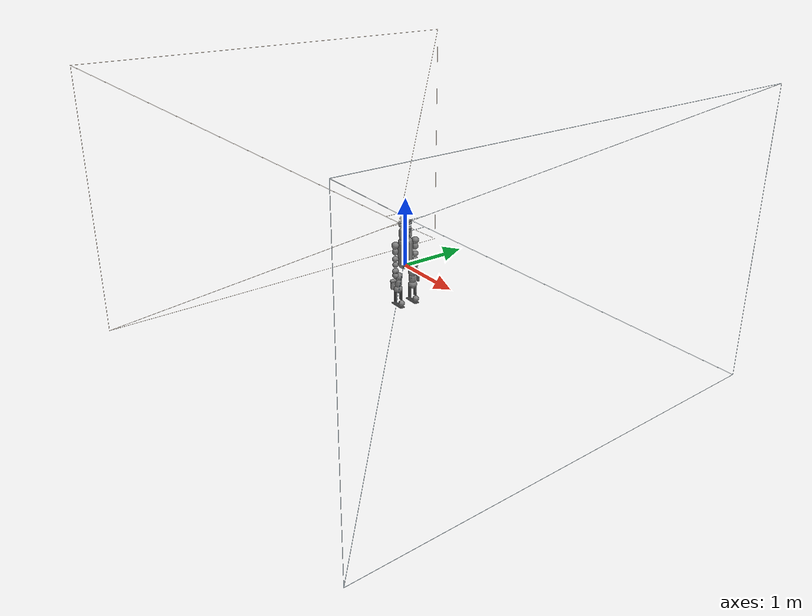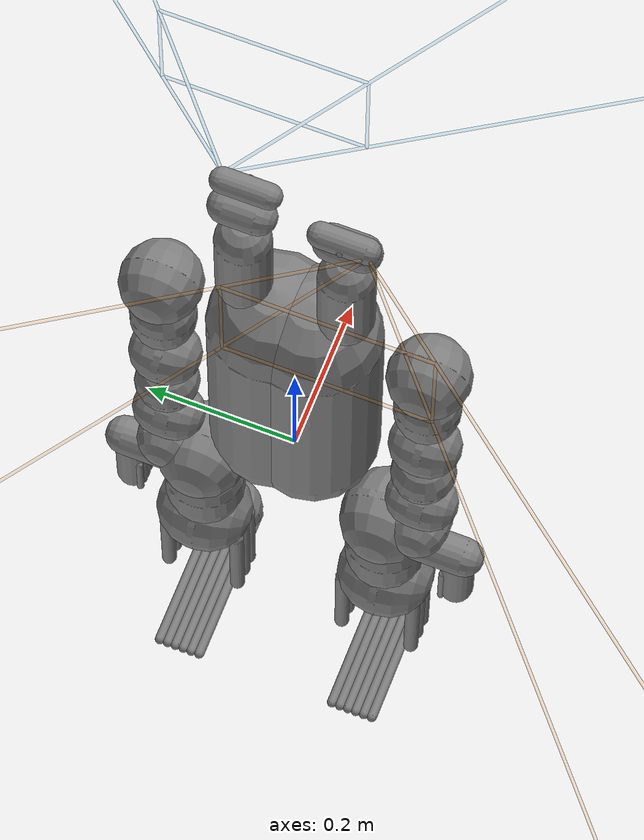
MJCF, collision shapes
<mujoco model="humanoid_v2">
  <compiler angle="radian" meshdir="/home/grl/repo/legged_env_v2/asset/duke_v2/humanoid_v21/meshes/" />
  <size nkey="1" />
  <default>
    <default class="humanoid_v2">
      <default class="visual">
        <geom type="mesh" contype="0" conaffinity="0" group="2" material="silver" />
      </default>
      <default class="collision">
        <geom group="3" />
      </default>
    </default>
    <default class="L_main">
      <default class="L_parallel_gripper">
        <default class="L_visual">
          <geom type="mesh" contype="0" conaffinity="0" group="2" material="silver" />
        </default>
        <default class="L_collision">
          <geom group="3" />
        </default>
      </default>
    </default>
    <default class="R_main">
      <default class="R_parallel_gripper">
        <default class="R_visual">
          <geom type="mesh" contype="0" conaffinity="0" group="2" material="silver" />
        </default>
        <default class="R_collision">
          <geom group="3" />
        </default>
      </default>
    </default>
    <default class="cam_main">
      <default class="cam_head_camera_dual">
        <default class="cam_visual">
          <geom type="mesh" contype="0" conaffinity="0" group="2" material="silver" />
        </default>
        <default class="cam_collision">
          <geom group="3" />
        </default>
      </default>
    </default>
  </default>
  <asset>
    <texture type="2d" colorspace="linear" name="L_tag_80_tex" file="/home/grl/repo/legged_env_v2/asset/duke_v2/parallel_gripper/meshes/tags/tag_80.png" />
    <texture type="2d" colorspace="linear" name="L_tag_81_tex" file="/home/grl/repo/legged_env_v2/asset/duke_v2/parallel_gripper/meshes/tags/tag_81.png" />
    <texture type="2d" colorspace="linear" name="L_tag_82_tex" file="/home/grl/repo/legged_env_v2/asset/duke_v2/parallel_gripper/meshes/tags/tag_82.png" />
    <texture type="2d" colorspace="linear" name="L_tag_83_tex" file="/home/grl/repo/legged_env_v2/asset/duke_v2/parallel_gripper/meshes/tags/tag_83.png" />
    <texture type="2d" colorspace="linear" name="L_tag_84_tex" file="/home/grl/repo/legged_env_v2/asset/duke_v2/parallel_gripper/meshes/tags/tag_84.png" />
    <texture type="2d" colorspace="linear" name="L_tag_85_tex" file="/home/grl/repo/legged_env_v2/asset/duke_v2/parallel_gripper/meshes/tags/tag_85.png" />
    <texture type="2d" colorspace="linear" name="L_tag_86_tex" file="/home/grl/repo/legged_env_v2/asset/duke_v2/parallel_gripper/meshes/tags/tag_86.png" />
    <texture type="2d" colorspace="linear" name="L_tag_87_tex" file="/home/grl/repo/legged_env_v2/asset/duke_v2/parallel_gripper/meshes/tags/tag_87.png" />
    <texture type="2d" colorspace="linear" name="R_tag_90_tex" file="/home/grl/repo/legged_env_v2/asset/duke_v2/parallel_gripper/meshes/tags/tag_90.png" />
    <texture type="2d" colorspace="linear" name="R_tag_91_tex" file="/home/grl/repo/legged_env_v2/asset/duke_v2/parallel_gripper/meshes/tags/tag_91.png" />
    <texture type="2d" colorspace="linear" name="R_tag_92_tex" file="/home/grl/repo/legged_env_v2/asset/duke_v2/parallel_gripper/meshes/tags/tag_92.png" />
    <texture type="2d" colorspace="linear" name="R_tag_93_tex" file="/home/grl/repo/legged_env_v2/asset/duke_v2/parallel_gripper/meshes/tags/tag_93.png" />
    <texture type="2d" colorspace="linear" name="R_tag_94_tex" file="/home/grl/repo/legged_env_v2/asset/duke_v2/parallel_gripper/meshes/tags/tag_94.png" />
    <texture type="2d" colorspace="linear" name="R_tag_95_tex" file="/home/grl/repo/legged_env_v2/asset/duke_v2/parallel_gripper/meshes/tags/tag_95.png" />
    <texture type="2d" colorspace="linear" name="R_tag_96_tex" file="/home/grl/repo/legged_env_v2/asset/duke_v2/parallel_gripper/meshes/tags/tag_96.png" />
    <texture type="2d" colorspace="linear" name="R_tag_97_tex" file="/home/grl/repo/legged_env_v2/asset/duke_v2/parallel_gripper/meshes/tags/tag_97.png" />
    <material name="silver" rgba="0.75 0.75 0.75 1" />
    <material name="blue" rgba="0 0 0.8 1" />
    <material name="black" rgba="0 0 0 1" />
    <material name="purple" rgba="0.8 0 0.8 1" />
    <material name="white" />
    <material name="light_grey" specular="0.75" shininess="0.05" rgba="0.19 0.2 0.22 1" />
    <material name="dark_grey" specular="0.35" shininess="0.05" rgba="0.11 0.115 0.125 1" />
    <material name="L_silver" rgba="0.75 0.75 0.75 1" />
    <material name="L_base_mat" specular="0.15" shininess="0.1" rgba="0.38 0.38 0.38 1" />
    <material name="L_left_rack_mat" specular="0.05" shininess="0.05" rgba="0.3 0.31 0.34 1" />
    <material name="L_right_rack_mat" specular="0.05" shininess="0.05" rgba="0.33 0.3 0.34 1" />
    <material name="L_tag_80_mat" texture="L_tag_80_tex" specular="0" shininess="0" />
    <material name="L_tag_81_mat" texture="L_tag_81_tex" specular="0" shininess="0" />
    <material name="L_tag_82_mat" texture="L_tag_82_tex" specular="0" shininess="0" />
    <material name="L_tag_83_mat" texture="L_tag_83_tex" specular="0" shininess="0" />
    <material name="L_tag_84_mat" texture="L_tag_84_tex" specular="0" shininess="0" />
    <material name="L_tag_85_mat" texture="L_tag_85_tex" specular="0" shininess="0" />
    <material name="L_tag_86_mat" texture="L_tag_86_tex" specular="0" shininess="0" />
    <material name="L_tag_87_mat" texture="L_tag_87_tex" specular="0" shininess="0" />
    <material name="R_silver" rgba="0.75 0.75 0.75 1" />
    <material name="R_base_mat" specular="0.15" shininess="0.1" rgba="0.38 0.38 0.38 1" />
    <material name="R_left_rack_mat" specular="0.05" shininess="0.05" rgba="0.3 0.31 0.34 1" />
    <material name="R_right_rack_mat" specular="0.05" shininess="0.05" rgba="0.33 0.3 0.34 1" />
    <material name="R_tag_90_mat" texture="R_tag_90_tex" specular="0" shininess="0" />
    <material name="R_tag_91_mat" texture="R_tag_91_tex" specular="0" shininess="0" />
    <material name="R_tag_92_mat" texture="R_tag_92_tex" specular="0" shininess="0" />
    <material name="R_tag_93_mat" texture="R_tag_93_tex" specular="0" shininess="0" />
    <material name="R_tag_94_mat" texture="R_tag_94_tex" specular="0" shininess="0" />
    <material name="R_tag_95_mat" texture="R_tag_95_tex" specular="0" shininess="0" />
    <material name="R_tag_96_mat" texture="R_tag_96_tex" specular="0" shininess="0" />
    <material name="R_tag_97_mat" texture="R_tag_97_tex" specular="0" shininess="0" />
    <material name="cam_silver" rgba="0.75 0.75 0.75 1" />
    <material name="cam_blue" rgba="0 0 0.8 1" />
    <material name="cam_black" rgba="0 0 0 1" />
    <material name="cam_purple" rgba="0.8 0 0.8 1" />
    <material name="cam_white" />
    <material name="cam_light_grey" specular="0.75" shininess="0.05" rgba="0.19 0.2 0.22 1" />
    <material name="cam_dark_grey" specular="0.35" shininess="0.05" rgba="0.11 0.115 0.125 1" />
    <material name="cam_d436" specular="0.75" shininess="0.2" rgba="0.58 0.6 0.62 1" />
    <mesh name="base_link" file="base_link.stl" scale="0.001 0.001 0.001" />
    <mesh name="waist_high_res" content_type="model/obj" file="waist.obj" scale="0.001 0.001 0.001" />
    <mesh name="hip_2_high_res_mirrorx" content_type="model/obj" file="hip_2.obj" scale="-0.001 0.001 0.001" />
    <mesh name="hip_2_high_res" file="hip_2.obj" scale="0.001 0.001 0.001" />
    <mesh name="hip_3_high_res_mirrorx" content_type="model/obj" file="hip_3.obj" scale="-0.001 0.001 0.001" />
    <mesh name="hip_3_high_res" file="hip_3.obj" scale="0.001 0.001 0.001" />
    <mesh name="knee_high_res_mirrorx" file="knee.obj" scale="-0.001 0.001 0.001" />
    <mesh name="knee_high_res" content_type="model/obj" file="knee.obj" scale="0.001 0.001 0.001" />
    <mesh name="shank_high_res_mirrorx" file="shank.obj" scale="-0.001 0.001 0.001" />
    <mesh name="shank_high_res" content_type="model/obj" file="shank.obj" scale="0.001 0.001 0.001" />
    <mesh name="ankle_1_high_res_mirrorx" file="ankle_1.obj" scale="-0.001 0.001 0.001" />
    <mesh name="ankle_1_high_res" content_type="model/obj" file="ankle_1.obj" scale="0.001 0.001 0.001" />
    <mesh name="ankle_2_high_res_mirrorx" content_type="model/obj" file="ankle_2.obj" scale="-0.001 0.001 0.001" />
    <mesh name="ankle_2_high_res" file="ankle_2.obj" scale="0.001 0.001 0.001" />
    <mesh name="shoulder_2_high_res_mirrorx" content_type="model/obj" file="shoulder_2.obj" scale="-0.001 0.001 0.001" />
    <mesh name="shoulder_2_high_res" file="shoulder_2.obj" scale="0.001 0.001 0.001" />
    <mesh name="shoulder_3_high_res_mirrorx" content_type="model/obj" file="shoulder_3.obj" scale="-0.001 0.001 0.001" />
    <mesh name="shoulder_3_high_res" file="shoulder_3.obj" scale="0.001 0.001 0.001" />
    <mesh name="elbow_high_res_mirrorx" file="elbow.obj" scale="-0.001 0.001 0.001" />
    <mesh name="elbow_high_res" content_type="model/obj" file="elbow.obj" scale="0.001 0.001 0.001" />
    <mesh name="wrist_1_high_res_mirrorx" file="wrist_1.obj" scale="-0.001 0.001 0.001" />
    <mesh name="wrist_1_high_res" content_type="model/obj" file="wrist_1.obj" scale="0.001 0.001 0.001" />
    <mesh name="wrist_2_high_res_mirrorx" content_type="model/obj" file="wrist_2.obj" scale="-0.001 0.001 0.001" />
    <mesh name="wrist_2_high_res" file="wrist_2.obj" scale="0.001 0.001 0.001" />
    <mesh name="wrist_3_new_high_res_mirrorx" file="wrist_3_new.obj" scale="-0.001 0.001 0.001" />
    <mesh name="wrist_3_new_high_res" content_type="model/obj" file="wrist_3_new.obj" scale="0.001 0.001 0.001" />
    <mesh name="end_effector_attachment_new_high_res_mirrorx" file="end_effector_attachment_new.obj" scale="-0.001 0.001 0.001" />
    <mesh name="end_effector_attachment_new_high_res" content_type="model/obj" file="end_effector_attachment_new.obj" scale="0.001 0.001 0.001" />
    <mesh name="L_base" file="/home/grl/repo/legged_env_v2/asset/duke_v2/parallel_gripper/meshes/base.obj" scale="0.001 0.001 0.001" />
    <mesh name="L_left_rack" file="/home/grl/repo/legged_env_v2/asset/duke_v2/parallel_gripper/meshes/left_rack.obj" scale="0.001 0.001 0.001" />
    <mesh name="L_right_rack" file="/home/grl/repo/legged_env_v2/asset/duke_v2/parallel_gripper/meshes/right_rack.obj" scale="0.001 0.001 0.001" />
    <mesh name="L_tag_80_quad" file="/home/grl/repo/legged_env_v2/asset/duke_v2/parallel_gripper/meshes/tags/tag_80.obj" inertia="shell" scale="0.001 0.001 0.001" />
    <mesh name="L_tag_81_quad" file="/home/grl/repo/legged_env_v2/asset/duke_v2/parallel_gripper/meshes/tags/tag_81.obj" inertia="shell" scale="0.001 0.001 0.001" />
    <mesh name="L_tag_82_quad" file="/home/grl/repo/legged_env_v2/asset/duke_v2/parallel_gripper/meshes/tags/tag_82.obj" inertia="shell" scale="0.001 0.001 0.001" />
    <mesh name="L_tag_83_quad" file="/home/grl/repo/legged_env_v2/asset/duke_v2/parallel_gripper/meshes/tags/tag_83.obj" inertia="shell" scale="0.001 0.001 0.001" />
    <mesh name="L_tag_84_quad" file="/home/grl/repo/legged_env_v2/asset/duke_v2/parallel_gripper/meshes/tags/tag_84.obj" inertia="shell" scale="0.001 0.001 0.001" />
    <mesh name="L_tag_85_quad" file="/home/grl/repo/legged_env_v2/asset/duke_v2/parallel_gripper/meshes/tags/tag_85.obj" inertia="shell" scale="0.001 0.001 0.001" />
    <mesh name="L_tag_86_quad" file="/home/grl/repo/legged_env_v2/asset/duke_v2/parallel_gripper/meshes/tags/tag_86.obj" inertia="shell" scale="0.001 0.001 0.001" />
    <mesh name="L_tag_87_quad" file="/home/grl/repo/legged_env_v2/asset/duke_v2/parallel_gripper/meshes/tags/tag_87.obj" inertia="shell" scale="0.001 0.001 0.001" />
    <mesh name="R_base" file="/home/grl/repo/legged_env_v2/asset/duke_v2/parallel_gripper/meshes/base.obj" scale="0.001 0.001 0.001" />
    <mesh name="R_left_rack" file="/home/grl/repo/legged_env_v2/asset/duke_v2/parallel_gripper/meshes/left_rack.obj" scale="0.001 0.001 0.001" />
    <mesh name="R_right_rack" file="/home/grl/repo/legged_env_v2/asset/duke_v2/parallel_gripper/meshes/right_rack.obj" scale="0.001 0.001 0.001" />
    <mesh name="R_tag_90_quad" file="/home/grl/repo/legged_env_v2/asset/duke_v2/parallel_gripper/meshes/tags/tag_90.obj" inertia="shell" scale="0.001 0.001 0.001" />
    <mesh name="R_tag_91_quad" file="/home/grl/repo/legged_env_v2/asset/duke_v2/parallel_gripper/meshes/tags/tag_91.obj" inertia="shell" scale="0.001 0.001 0.001" />
    <mesh name="R_tag_92_quad" file="/home/grl/repo/legged_env_v2/asset/duke_v2/parallel_gripper/meshes/tags/tag_92.obj" inertia="shell" scale="0.001 0.001 0.001" />
    <mesh name="R_tag_93_quad" file="/home/grl/repo/legged_env_v2/asset/duke_v2/parallel_gripper/meshes/tags/tag_93.obj" inertia="shell" scale="0.001 0.001 0.001" />
    <mesh name="R_tag_94_quad" file="/home/grl/repo/legged_env_v2/asset/duke_v2/parallel_gripper/meshes/tags/tag_94.obj" inertia="shell" scale="0.001 0.001 0.001" />
    <mesh name="R_tag_95_quad" file="/home/grl/repo/legged_env_v2/asset/duke_v2/parallel_gripper/meshes/tags/tag_95.obj" inertia="shell" scale="0.001 0.001 0.001" />
    <mesh name="R_tag_96_quad" file="/home/grl/repo/legged_env_v2/asset/duke_v2/parallel_gripper/meshes/tags/tag_96.obj" inertia="shell" scale="0.001 0.001 0.001" />
    <mesh name="R_tag_97_quad" file="/home/grl/repo/legged_env_v2/asset/duke_v2/parallel_gripper/meshes/tags/tag_97.obj" inertia="shell" scale="0.001 0.001 0.001" />
    <mesh name="cam_base_left" content_type="model/obj" file="/home/grl/repo/legged_env_v2/asset/duke_v2/head_cam/meshes/links/base_left.obj" scale="0.001 0.001 0.001" />
    <mesh name="cam_yaw_left" file="/home/grl/repo/legged_env_v2/asset/duke_v2/head_cam/meshes/links/yaw_left.obj" scale="0.001 0.001 0.001" />
    <mesh name="cam_pitch_left_bracket" file="/home/grl/repo/legged_env_v2/asset/duke_v2/head_cam/meshes/links/pitch_left_bracket.obj" scale="0.001 0.001 0.001" />
    <mesh name="cam_pitch_left_d436" file="/home/grl/repo/legged_env_v2/asset/duke_v2/head_cam/meshes/links/pitch_left_d436.obj" scale="0.001 0.001 0.001" />
  </asset>
  <worldbody>
    <body name="base_link" childclass="humanoid_v2">
      <inertial pos="-0.00741636 4.16161e-05 0.186843" quat="8.35609e-05 0.718034 -0.000326247 0.696008" mass="9.30291" diaginertia="0.0347794 0.173949 0.189052" />
      <joint name="floating_base_joint" type="free" />
      <geom name="base_link_visual" class="visual" material="dark_grey" mesh="base_link" />
      <geom name="base_link_collision0" class="collision" size="0.0848538 0.155146" pos="0 -0.0249986 0.2" type="capsule" condim="1" />
      <geom name="base_link_collision1" class="collision" size="0.0848538 0.155146" pos="0 0.0249986 0.2" type="capsule" condim="1" />
      <site name="imu_site" pos="0 0 0" />
      <camera name="tracking" pos="1.5 -1.5 1" quat="0.780227 0.494771 0.204941 0.323181" mode="trackcom" />
      <light pos="0 0 2" dir="0 0 -1" castshadow="false" mode="trackcom" />
      <body name="waist" pos="0 0 -0.0361">
        <inertial pos="-0.00238207 4.63475e-07 -0.0704721" quat="-0.43413 0.558388 0.558062 -0.433936" mass="2.31937" diaginertia="0.00376271 0.00529885 0.00558094" />
        <joint name="waist_joint" pos="0 0 0" axis="0 0 1" range="-1.5708 1.5708" armature="0.02" frictionloss="0.2" />
        <geom name="waist_visual" class="visual" material="dark_grey" mesh="waist_high_res" />
        <body name="hip_2_L" pos="0 0.059946 -0.081628" quat="0.793353 0.608761 0 0">
          <inertial pos="0.000349087 2.18694e-05 -0.061261" quat="0.536837 0.540342 0.45664 -0.459691" mass="1.2527" diaginertia="0.00138225 0.00185815 0.00192888" />
          <joint name="left_hip_1_joint" pos="0 0 0" axis="0 0 1" range="-1.8326 1.8326" armature="0.02" frictionloss="0.2" />
          <geom name="hip_2_L_visual" class="visual" quat="0 0 0 1" material="light_grey" mesh="hip_2_high_res_mirrorx" />
          <geom name="hip_2_L_collision" class="collision" size="0.06 0.005" pos="0.0006 0 -0.069" quat="0.092296 0.701057 -0.092296 -0.701057" type="capsule" condim="1" />
          <body name="hip_3_L" pos="0.0287 0 -0.0691" quat="0.701057 0.092296 -0.701057 -0.092296">
            <inertial pos="-2.07731e-05 -0.0770614 0.0307231" quat="0.51929 -0.479853 -0.519071 0.480255" mass="1.29734" diaginertia="0.00175068 0.00229469 0.00271565" />
            <joint name="left_hip_2_joint" pos="0 0 0" axis="0 0 1" range="-1.8326 0.523599" armature="0.02" frictionloss="0.5" />
            <geom name="hip_3_L_visual" class="visual" material="dark_grey" mesh="hip_3_high_res_mirrorx" />
            <geom name="hip_3_L_collision" class="collision" size="0.053 0.021" pos="0 -0.0945 0.0287" quat="0.707107 -0.707107 0 0" type="capsule" condim="1" />
            <body name="knee_L" pos="0 -0.1156 0.0287" quat="0.707107 -0.707107 0 0">
              <inertial pos="0.0014826 -8.41853e-05 -0.0736603" quat="-0.00022525 0.722024 0.00337258 -0.69186" mass="1.84214" diaginertia="0.00190901 0.00264702 0.00341994" />
              <joint name="left_hip_3_joint" pos="0 0 0" axis="0 0 1" range="-1.5708 1.5708" armature="0.02" frictionloss="0.2" />
              <geom name="knee_L_visual" class="visual" quat="0 0 0 1" material="light_grey" mesh="knee_high_res_mirrorx" />
              <geom name="knee_L_collision" class="collision" size="0.06 0.005" pos="-0.00225 0 -0.0795" quat="0.5 -0.5 -0.5 0.5" type="capsule" condim="1" />
              <body name="shank_L" pos="0.0255 0 -0.0795" quat="0.5 -0.5 -0.5 0.5">
                <inertial pos="-8.59033e-07 0.0943751 0.0229906" quat="0.498696 0.501311 -0.498686 -0.5013" mass="0.753289" diaginertia="0.00154563 0.00486086 0.00599117" />
                <joint name="left_knee_joint" pos="0 0 0" axis="0 0 1" range="-2.26893 2.26893" armature="0.04" frictionloss="0.5" />
                <geom name="shank_L_visual" class="visual" material="dark_grey" mesh="shank_high_res_mirrorx" />
                <geom name="shank_L_collision0" class="collision" size="0.01 0.08" pos="-0.02 0.1 -0.025" quat="0.707107 -0.707107 0 0" type="capsule" condim="1" />
                <geom name="shank_L_collision1" class="collision" size="0.01 0.08" pos="0 0.1 -0.025" quat="0.707107 -0.707107 0 0" type="capsule" condim="1" />
                <geom name="shank_L_collision2" class="collision" size="0.01 0.08" pos="0.02 0.1 -0.025" quat="0.707107 -0.707107 0 0" type="capsule" condim="1" />
                <geom name="shank_L_collision3" class="collision" size="0.01 0.08" pos="-0.02 0.1 0.075" quat="0.707107 -0.707107 0 0" type="capsule" condim="1" />
                <geom name="shank_L_collision4" class="collision" size="0.01 0.08" pos="0 0.1 0.075" quat="0.707107 -0.707107 0 0" type="capsule" condim="1" />
                <geom name="shank_L_collision5" class="collision" size="0.01 0.08" pos="0.02 0.1 0.075" quat="0.707107 -0.707107 0 0" type="capsule" condim="1" />
                <body name="ankle_1_L" pos="0 0.195 0" quat="0 0 1 0">
                  <inertial pos="-0.0305888 1.59279e-05 -0.025774" quat="0.00120435 0.999999 0.000123663 -0.000389805" mass="1.80186" diaginertia="0.00144542 0.00421361 0.00443807" />
                  <joint name="left_ankle_1_joint" pos="0 0 0" axis="0 0 1" range="-0.872665 0.872665" armature="0.02" frictionloss="0.2" />
                  <geom name="ankle_1_L_visual" class="visual" pos="0 0 0" quat="0 0 0 1" material="light_grey" mesh="ankle_1_high_res_mirrorx" />
                  <geom name="ankle_1_L_collision" class="collision" size="0.044 0.0005" pos="-0.08275 0 -0.0255" quat="0 -0.707107 0 -0.707107" type="capsule" condim="1" />
                  <body name="foot_L" pos="-0.1 0 -0.0255" quat="0.5 -0.5 0.5 -0.5">
                    <inertial pos="-0.0374774 -8.96073e-10 0.0957522" quat="0.489663 0.489663 -0.510128 0.510128" mass="0.506071" diaginertia="0.00061045 0.00341987 0.00361595" />
                    <joint name="left_ankle_2_joint" pos="0 0 0" axis="0 0 1" range="-1.0472 1.0472" armature="0.012" frictionloss="0.5" />
                    <geom name="foot_L_visual" class="visual" pos="0 0 0" quat="0 0 0 1" material="dark_grey" mesh="ankle_2_high_res_mirrorx" />
                    <geom name="foot_L_collision0" class="collision" size="0.007 0.1105" pos="-0.061 0.029 0.1" quat="0 0 0 1" type="capsule" priority="1" solref="0.01" solimp="0.9 0.95 0.005" />
                    <geom name="foot_L_collision1" class="collision" size="0.007 0.1105" pos="-0.061 0.0174 0.1" quat="0 0 0 1" type="capsule" priority="1" solref="0.01" solimp="0.9 0.95 0.005" />
                    <geom name="foot_L_collision2" class="collision" size="0.007 0.1105" pos="-0.061 0.0058 0.1" quat="0 0 0 1" type="capsule" priority="1" solref="0.01" solimp="0.9 0.95 0.005" />
                    <geom name="foot_L_collision3" class="collision" size="0.007 0.1105" pos="-0.061 -0.0058 0.1" quat="0 0 0 1" type="capsule" priority="1" solref="0.01" solimp="0.9 0.95 0.005" />
                    <geom name="foot_L_collision4" class="collision" size="0.007 0.1105" pos="-0.061 -0.0174 0.1" quat="0 0 0 1" type="capsule" priority="1" solref="0.01" solimp="0.9 0.95 0.005" />
                    <geom name="foot_L_collision5" class="collision" size="0.007 0.1105" pos="-0.061 -0.029 0.1" quat="0 0 0 1" type="capsule" priority="1" solref="0.01" solimp="0.9 0.95 0.005" />
                    <site name="foot_L_contact" pos="-0.061 0 0.1" />
                  </body>
                </body>
              </body>
            </body>
          </body>
        </body>
        <body name="hip_2_R" pos="0 -0.059946 -0.081628" quat="0.793353 -0.608761 0 0">
          <inertial pos="0.000349087 -2.18694e-05 -0.061261" quat="-0.459691 0.45664 0.540342 0.536837" mass="1.2527" diaginertia="0.00138225 0.00185815 0.00192888" />
          <joint name="right_hip_1_joint" pos="0 0 0" axis="0 0 1" range="-1.8326 1.8326" armature="0.02" frictionloss="0.2" />
          <geom name="hip_2_R_visual" class="visual" material="light_grey" mesh="hip_2_high_res" />
          <geom name="hip_2_R_collision" class="collision" size="0.06 0.005" pos="0.0006 0 -0.069" quat="0.701057 0.092296 -0.701057 -0.092296" type="capsule" condim="1" />
          <body name="hip_3_R" pos="0.0287 0 -0.0691" quat="0.092296 0.701057 -0.092296 -0.701057">
            <inertial pos="2.07731e-05 -0.0770614 0.0307231" quat="0.519071 -0.480255 -0.51929 0.479853" mass="1.29734" diaginertia="0.00175068 0.00229469 0.00271565" />
            <joint name="right_hip_2_joint" pos="0 0 0" axis="0 0 1" range="-0.523599 1.8326" armature="0.02" frictionloss="0.5" />
            <geom name="hip_3_R_visual" class="visual" material="dark_grey" mesh="hip_3_high_res" />
            <geom name="hip_3_R_collision" class="collision" size="0.053 0.021" pos="0 -0.0945 0.0287" quat="0.707107 -0.707107 0 0" type="capsule" condim="1" />
            <body name="knee_R" pos="0 -0.1156 0.0287" quat="0 0 0.707107 0.707107">
              <inertial pos="0.0014826 8.41853e-05 -0.0736603" quat="0.69186 -0.00337258 -0.722024 0.00022525" mass="1.84214" diaginertia="0.00190901 0.00264702 0.00341994" />
              <joint name="right_hip_3_joint" pos="0 0 0" axis="0 0 1" range="-1.5708 1.5708" armature="0.02" frictionloss="0.2" />
              <geom name="knee_R_visual" class="visual" material="light_grey" mesh="knee_high_res" />
              <geom name="knee_R_collision" class="collision" size="0.06 0.005" pos="-0.00225 0 -0.0795" quat="0.5 -0.5 -0.5 0.5" type="capsule" condim="1" />
              <body name="shank_R" pos="0.0255 0 -0.0795" quat="0.5 -0.5 -0.5 0.5">
                <inertial pos="8.59033e-07 0.0943751 0.0229906" quat="-0.498686 -0.5013 0.498696 0.501311" mass="0.753289" diaginertia="0.00154563 0.00486086 0.00599117" />
                <joint name="right_knee_joint" pos="0 0 0" axis="0 0 1" range="-2.26893 2.26893" armature="0.04" frictionloss="0.5" />
                <geom name="shank_R_visual" class="visual" material="dark_grey" mesh="shank_high_res" />
                <geom name="shank_R_collision0" class="collision" size="0.01 0.08" pos="-0.02 0.1 -0.025" quat="0.707107 -0.707107 0 0" type="capsule" condim="1" />
                <geom name="shank_R_collision1" class="collision" size="0.01 0.08" pos="0 0.1 -0.025" quat="0.707107 -0.707107 0 0" type="capsule" condim="1" />
                <geom name="shank_R_collision2" class="collision" size="0.01 0.08" pos="0.02 0.1 -0.025" quat="0.707107 -0.707107 0 0" type="capsule" condim="1" />
                <geom name="shank_R_collision3" class="collision" size="0.01 0.08" pos="-0.02 0.1 0.075" quat="0.707107 -0.707107 0 0" type="capsule" condim="1" />
                <geom name="shank_R_collision4" class="collision" size="0.01 0.08" pos="0 0.1 0.075" quat="0.707107 -0.707107 0 0" type="capsule" condim="1" />
                <geom name="shank_R_collision5" class="collision" size="0.01 0.08" pos="0.02 0.1 0.075" quat="0.707107 -0.707107 0 0" type="capsule" condim="1" />
                <body name="ankle_1_R" pos="0 0.195 0" quat="0 -1 0 0">
                  <inertial pos="-0.0305888 -1.59279e-05 -0.025774" quat="0.999999 0.00120435 0.000389805 -0.000123663" mass="1.80186" diaginertia="0.00144542 0.00421361 0.00443807" />
                  <joint name="right_ankle_1_joint" pos="0 0 0" axis="0 0 1" range="-0.872665 0.872665" armature="0.02" frictionloss="0.2" />
                  <geom name="ankle_1_R_visual" class="visual" material="light_grey" mesh="ankle_1_high_res" />
                  <geom name="ankle_1_R_collision" class="collision" size="0.044 0.0005" pos="-0.08275 0 -0.0255" quat="0.707107 0 0.707107 0" type="capsule" condim="1" />
                  <body name="foot_R" pos="-0.1 0 -0.0255" quat="0.5 0.5 0.5 0.5">
                    <inertial pos="-0.0374774 8.96073e-10 0.0957522" quat="0.489663 0.489663 -0.510128 0.510128" mass="0.506071" diaginertia="0.00061045 0.00341987 0.00361595" />
                    <joint name="right_ankle_2_joint" pos="0 0 0" axis="0 0 1" range="-1.0472 1.0472" armature="0.012" frictionloss="0.5" />
                    <geom name="foot_R_visual" class="visual" material="dark_grey" mesh="ankle_2_high_res" />
                    <geom name="foot_R_collision0" class="collision" size="0.007 0.1105" pos="-0.061 -0.029 0.1" type="capsule" priority="1" solref="0.01" solimp="0.9 0.95 0.005" />
                    <geom name="foot_R_collision1" class="collision" size="0.007 0.1105" pos="-0.061 -0.0174 0.1" type="capsule" priority="1" solref="0.01" solimp="0.9 0.95 0.005" />
                    <geom name="foot_R_collision2" class="collision" size="0.007 0.1105" pos="-0.061 -0.0058 0.1" type="capsule" priority="1" solref="0.01" solimp="0.9 0.95 0.005" />
                    <geom name="foot_R_collision3" class="collision" size="0.007 0.1105" pos="-0.061 0.0058 0.1" type="capsule" priority="1" solref="0.01" solimp="0.9 0.95 0.005" />
                    <geom name="foot_R_collision4" class="collision" size="0.007 0.1105" pos="-0.061 0.0174 0.1" type="capsule" priority="1" solref="0.01" solimp="0.9 0.95 0.005" />
                    <geom name="foot_R_collision5" class="collision" size="0.007 0.1105" pos="-0.061 0.029 0.1" type="capsule" priority="1" solref="0.01" solimp="0.9 0.95 0.005" />
                    <site name="foot_R_contact" pos="-0.061 0 0.1" />
                  </body>
                </body>
              </body>
            </body>
          </body>
        </body>
      </body>
      <body name="shoulder_2_L" pos="0 0.083 0.3475" quat="0.707107 0.707107 0 0">
        <inertial pos="0.000787068 5.71455e-07 -0.0730081" quat="-4.15531e-05 0.677536 2.98517e-05 0.73549" mass="0.903097" diaginertia="0.000555624 0.00146696 0.00153275" />
        <joint name="left_shoulder_1_joint" pos="0 0 0" axis="0 0 1" range="-3.14159 3.14159" armature="0.02" frictionloss="0.5" />
        <geom name="shoulder_2_L_visual" class="visual" quat="0 0 0 1" material="dark_grey" mesh="shoulder_2_high_res_mirrorx" />
        <geom name="shoulder_2_L_collision" class="collision" size="0.053 5e-05" pos="0 0 -0.09" quat="0 -0.707107 0 -0.707107" type="capsule" condim="1" />
        <body name="shoulder_3_L" pos="0.02475 0 -0.09" quat="0.707107 0 -0.707107 0">
          <inertial pos="-0.000428244 -0.0657202 0.0269038" quat="-0.493187 0.508665 0.504716 -0.493242" mass="0.716054" diaginertia="0.000675965 0.00100372 0.00122933" />
          <joint name="left_shoulder_2_joint" pos="0 0 0" axis="0 0 1" range="-3.14159 0.523599" armature="0.012" frictionloss="0.2" />
          <geom name="shoulder_3_L_visual" class="visual" material="light_grey" mesh="shoulder_3_high_res_mirrorx" />
          <geom name="shoulder_3_L_collision" class="collision" size="0.042 0.01" pos="0 -0.093 0.02475" quat="0.707107 0.707107 0 0" type="capsule" condim="1" />
          <body name="elbow_L" pos="0 -0.096 0.02475" quat="0 0 0.707107 0.707107">
            <inertial pos="0.00165016 -0.0024442 -0.0943709" quat="0.734796 0.086108 0.672778 -0.00554098" mass="0.649565" diaginertia="0.000376826 0.000924704 0.00107426" />
            <joint name="left_shoulder_3_joint" pos="0 0 0" axis="0 0 1" range="-3.14159 3.14159" armature="0.0042" frictionloss="0.1" />
            <geom name="elbow_L_visual" class="visual" quat="0 0 0 1" material="dark_grey" mesh="elbow_high_res_mirrorx" />
            <geom name="elbow_L_collision" class="collision" size="0.042 0.005" pos="0 0 -0.111" quat="0 -0.707107 0 -0.707107" type="capsule" condim="1" />
            <body name="wrist_1_L" pos="0 0 -0.111" quat="0.5 0.5 -0.5 -0.5">
              <inertial pos="0.000186448 -0.0651533 0.00301697" quat="0.458603 0.539817 -0.475968 -0.521282" mass="0.745374" diaginertia="0.000704132 0.00105686 0.00129828" />
              <joint name="left_elbow_joint" pos="0 0 0" axis="0 0 1" range="-2.18166 2.18166" armature="0.0042" frictionloss="0.1" />
              <geom name="wrist_1_L_visual" class="visual" material="light_grey" mesh="wrist_1_high_res_mirrorx" />
              <geom name="wrist_1_L_collision" class="collision" size="0.042 5e-05" pos="0 -0.0885 0" quat="0.707107 0.707107 0 0" type="capsule" condim="1" />
              <body name="wrist_2_L" pos="0 -0.096 0" quat="0.5 -0.5 -0.5 -0.5">
                <inertial pos="-0.00845747 2.17826e-05 -0.0781628" quat="0.475646 0.475072 0.524297 -0.522667" mass="0.446371" diaginertia="0.000202786 0.000381248 0.000403138" />
                <joint name="left_wrist_1_joint" pos="0 0 0" axis="0 0 1" range="-3.14159 3.14159" armature="0.0042" frictionloss="0.1" />
                <geom name="wrist_2_L_visual" class="visual" quat="0 0 0 1" material="dark_grey" mesh="wrist_2_high_res_mirrorx" />
                <geom name="wrist_2_L_collision" class="collision" size="0.038 0.01" pos="0 0 -0.0855" quat="0 -0.707107 0 -0.707107" type="capsule" condim="1" />
                <body name="wrist_3_L" pos="0 0 -0.0855" quat="0 0 0 1">
                  <inertial pos="-0.00698731 -0.00907562 -0.0474171" quat="0.817224 -0.0872787 0.56821 -0.0408068" mass="0.352354" diaginertia="0.000125529 0.000440978 0.000444273" />
                  <joint name="left_wrist_2_joint" pos="0 0 0" axis="-1 0 0" range="-1.6057 1.6057" armature="0.0007" frictionloss="0.05" />
                  <geom name="wrist_3_L_visual" class="visual" material="light_grey" mesh="wrist_3_new_high_res_mirrorx" />
                  <geom name="wrist_3_L_collision" class="collision" size="0.04 0.01" pos="0 0 -0.07" quat="0.707107 0.707107 0 0" type="capsule" condim="1" />
                  <body name="end_effector_L" pos="0 0 -0.064" quat="0.5 0.5 0.5 -0.5">
                    <inertial pos="0.01513 2.418e-08 -0.01529" quat="0.992481 -3.04069e-06 -0.122399 3.74997e-07" mass="0.17299" diaginertia="5.85506e-05 0.00014 0.000145109" />
                    <joint name="left_wrist_3_joint" pos="0 0 0" axis="0 0 1" range="-1.5708 1.5708" armature="0.001" frictionloss="0.05" />
                    <geom name="end_effector_L_visual" class="visual" quat="0 0 0 1" material="dark_grey" mesh="end_effector_attachment_new_high_res_mirrorx" />
                    <site name="end_effector_L_site" pos="0.169 0.00096 0" />
                    <body name="L_base" childclass="L_parallel_gripper" pos="0.079 -0.006 0.01">
                      <inertial pos="0.000733468 0.0119563 -0.00964551" quat="0.725257 0.023573 0.00705184 -0.688038" mass="0.171609" diaginertia="4.99918e-05 0.000207737 0.000223325" />
                      <geom name="L_base_visual" class="L_visual" material="L_base_mat" mesh="L_base" />
                      <geom name="L_base_collision" class="L_collision" size="0.026 0.064" pos="-0.0017 0.0075 -0.01" quat="0.707107 -0.707107 0 0" type="capsule" condim="1" />
                      <geom name="L_tag_84" type="mesh" contype="0" conaffinity="0" group="2" material="L_tag_84_mat" mesh="L_tag_84_quad" />
                      <geom name="L_tag_85" type="mesh" contype="0" conaffinity="0" group="2" material="L_tag_85_mat" mesh="L_tag_85_quad" />
                      <geom name="L_tag_86" type="mesh" contype="0" conaffinity="0" group="2" material="L_tag_86_mat" mesh="L_tag_86_quad" />
                      <geom name="L_tag_87" type="mesh" contype="0" conaffinity="0" group="2" material="L_tag_87_mat" mesh="L_tag_87_quad" />
                      <body name="L_left_rack">
                        <inertial pos="0.0462025 -0.0220002 -0.00385734" quat="-0.0935321 0.426555 0.899548 0.0108181" mass="0.0743656" diaginertia="4.74015e-05 0.00012138 0.000153873" />
                        <joint name="L_left_rack_y" pos="0 0 0" axis="0 1 0" type="slide" range="-0.05 0.0347" armature="0.02" damping="12" />
                        <geom name="L_left_rack_visual" class="L_visual" material="L_left_rack_mat" mesh="L_left_rack" />
                        <geom name="L_left_rack_collision0" class="L_collision" size="0.005 0.0358" pos="0.0808 -0.033 -0.0249897" quat="0.707107 0 0.707107 0" type="capsule" conaffinity="0" friction="0.5" solref="0.005" />
                        <geom name="L_left_rack_collision1" class="L_collision" size="0.005 0.0358" pos="0.0808 -0.033 -0.0149966" quat="0.707107 0 0.707107 0" type="capsule" conaffinity="0" friction="0.5" solref="0.005" />
                        <geom name="L_left_rack_collision2" class="L_collision" size="0.005 0.0358" pos="0.0808 -0.033 -0.00500342" quat="0.707107 0 0.707107 0" type="capsule" conaffinity="0" friction="0.5" solref="0.005" />
                        <geom name="L_left_rack_collision3" class="L_collision" size="0.005 0.0358" pos="0.0808 -0.033 0.00498975" quat="0.707107 0 0.707107 0" type="capsule" conaffinity="0" friction="0.5" solref="0.005" />
                        <geom name="L_left_rack_collision4" class="L_collision" size="0.021 0.0225" pos="0.0675 -0.049 -0.01" quat="0.707107 0 0.707107 0" type="capsule" conaffinity="0" friction="0.5" solref="0.005" />
                        <geom name="L_left_rack_ikproxy" class="L_collision" size="0.0226 0.0458" pos="0.0608 -0.0486 -0.01" quat="0.707107 0 0.707107 0" type="capsule" contype="0" conaffinity="0" group="5" friction="2" solref="0.005" />
                        <geom name="L_tag_80" type="mesh" contype="0" conaffinity="0" group="2" material="L_tag_80_mat" mesh="L_tag_80_quad" />
                        <geom name="L_tag_81" type="mesh" contype="0" conaffinity="0" group="2" material="L_tag_81_mat" mesh="L_tag_81_quad" />
                      </body>
                      <body name="L_right_rack">
                        <inertial pos="0.0461618 0.0359459 -0.0161427" quat="-0.0107055 0.899312 0.427027 0.0936506" mass="0.0743656" diaginertia="4.73679e-05 0.000121196 0.000153672" />
                        <joint name="L_right_rack_y" pos="0 0 0" axis="0 -1 0" type="slide" range="-0.05 0.0347" armature="0.02" damping="12" />
                        <geom name="L_right_rack_visual" class="L_visual" material="L_right_rack_mat" mesh="L_right_rack" />
                        <geom name="L_right_rack_collision0" class="L_collision" size="0.005 0.0358" pos="0.0808 0.0469 -0.0249897" quat="0.707107 0 0.707107 0" type="capsule" conaffinity="0" friction="0.5" solref="0.005" />
                        <geom name="L_right_rack_collision1" class="L_collision" size="0.005 0.0358" pos="0.0808 0.0469 -0.0149966" quat="0.707107 0 0.707107 0" type="capsule" conaffinity="0" friction="0.5" solref="0.005" />
                        <geom name="L_right_rack_collision2" class="L_collision" size="0.005 0.0358" pos="0.0808 0.0469 -0.00500342" quat="0.707107 0 0.707107 0" type="capsule" conaffinity="0" friction="0.5" solref="0.005" />
                        <geom name="L_right_rack_collision3" class="L_collision" size="0.005 0.0358" pos="0.0808 0.0469 0.00498975" quat="0.707107 0 0.707107 0" type="capsule" conaffinity="0" friction="0.5" solref="0.005" />
                        <geom name="L_right_rack_collision4" class="L_collision" size="0.021 0.0225" pos="0.0675 0.0629 -0.01" quat="0.707107 0 0.707107 0" type="capsule" conaffinity="0" friction="0.5" solref="0.005" />
                        <geom name="L_right_rack_ikproxy" class="L_collision" size="0.0226 0.0458" pos="0.0608 0.0625 -0.01" quat="0.707107 0 0.707107 0" type="capsule" contype="0" conaffinity="0" group="5" friction="2" solref="0.005" />
                        <geom name="L_tag_82" type="mesh" contype="0" conaffinity="0" group="2" material="L_tag_82_mat" mesh="L_tag_82_quad" />
                        <geom name="L_tag_83" type="mesh" contype="0" conaffinity="0" group="2" material="L_tag_83_mat" mesh="L_tag_83_quad" />
                      </body>
                    </body>
                  </body>
                </body>
              </body>
            </body>
          </body>
        </body>
      </body>
      <body name="shoulder_2_R" pos="0 -0.083 0.3475" quat="0.707107 -0.707107 0 0">
        <inertial pos="0.000787068 -5.71455e-07 -0.0730081" quat="0.677536 -4.15531e-05 -0.73549 -2.98517e-05" mass="0.903097" diaginertia="0.000555624 0.00146696 0.00153275" />
        <joint name="right_shoulder_1_joint" pos="0 0 0" axis="0 0 1" range="-3.14159 3.14159" armature="0.02" frictionloss="0.5" />
        <geom name="shoulder_2_R_visual" class="visual" material="dark_grey" mesh="shoulder_2_high_res" />
        <geom name="shoulder_2_R_collision" class="collision" size="0.053 5e-05" pos="0 0 -0.09" quat="0.707107 0 0.707107 0" type="capsule" condim="1" />
        <body name="shoulder_3_R" pos="0.02475 0 -0.09" quat="0 0.707107 0 -0.707107">
          <inertial pos="0.000428244 -0.0657202 0.0269038" quat="0.504716 -0.493242 -0.493187 0.508665" mass="0.716054" diaginertia="0.000675965 0.00100372 0.00122933" />
          <joint name="right_shoulder_2_joint" pos="0 0 0" axis="0 0 1" range="-0.523599 3.14159" armature="0.012" frictionloss="0.2" />
          <geom name="shoulder_3_R_visual" class="visual" material="light_grey" mesh="shoulder_3_high_res" />
          <geom name="shoulder_3_R_collision" class="collision" size="0.042 0.01" pos="0 -0.093 0.02475" quat="0.707107 0.707107 0 0" type="capsule" condim="1" />
          <body name="elbow_R" pos="0 -0.096 0.02475" quat="0.707107 -0.707107 0 0">
            <inertial pos="0.00165016 0.0024442 -0.0943709" quat="0.086108 0.734796 0.00554098 -0.672778" mass="0.649565" diaginertia="0.000376826 0.000924704 0.00107426" />
            <joint name="right_shoulder_3_joint" pos="0 0 0" axis="0 0 1" range="-3.14159 3.14159" armature="0.0042" frictionloss="0.1" />
            <geom name="elbow_R_visual" class="visual" material="dark_grey" mesh="elbow_high_res" />
            <geom name="elbow_R_collision" class="collision" size="0.042 0.005" pos="0 0 -0.111" quat="0.707107 0 0.707107 0" type="capsule" condim="1" />
            <body name="wrist_1_R" pos="0 0 -0.111" quat="0.5 0.5 -0.5 -0.5">
              <inertial pos="-0.000186448 -0.0651533 0.00301697" quat="-0.475968 -0.521282 0.458603 0.539817" mass="0.745374" diaginertia="0.000704132 0.00105686 0.00129828" />
              <joint name="right_elbow_joint" pos="0 0 0" axis="0 0 1" range="-2.18166 2.18166" armature="0.0042" frictionloss="0.1" />
              <geom name="wrist_1_R_visual" class="visual" material="light_grey" mesh="wrist_1_high_res" />
              <geom name="wrist_1_R_collision" class="collision" size="0.042 5e-05" pos="0 -0.0885 0" quat="0.707107 0.707107 0 0" type="capsule" condim="1" />
              <body name="wrist_2_R" pos="0 -0.096 0" quat="0.5 -0.5 -0.5 -0.5">
                <inertial pos="-0.00845747 -2.17826e-05 -0.0781628" quat="0.522667 -0.524297 -0.475072 -0.475646" mass="0.446371" diaginertia="0.000202786 0.000381248 0.000403138" />
                <joint name="right_wrist_1_joint" pos="0 0 0" axis="0 0 1" range="-3.14159 3.14159" armature="0.0042" frictionloss="0.1" />
                <geom name="wrist_2_R_visual" class="visual" material="dark_grey" mesh="wrist_2_high_res" />
                <geom name="wrist_2_R_collision" class="collision" size="0.038 0.01" pos="0 0 -0.0855" quat="0.707107 0 0.707107 0" type="capsule" condim="1" />
                <body name="wrist_3_R" pos="0 0 -0.0855">
                  <inertial pos="0.00698731 -0.00907562 -0.0474171" quat="0.56821 -0.0408068 0.817224 -0.0872787" mass="0.352354" diaginertia="0.000125529 0.000440978 0.000444273" />
                  <joint name="right_wrist_2_joint" pos="0 0 0" axis="-1 0 0" range="-1.6057 1.6057" armature="0.0007" frictionloss="0.05" />
                  <geom name="wrist_3_R_visual" class="visual" material="light_grey" mesh="wrist_3_new_high_res" />
                  <geom name="wrist_3_R_collision" class="collision" size="0.04 0.01" pos="0 0 -0.07" quat="0.707107 0.707107 0 0" type="capsule" condim="1" />
                  <body name="end_effector_R" pos="0 0 -0.064" quat="0.5 0.5 0.5 -0.5">
                    <inertial pos="0.01513 -2.418e-08 -0.01529" quat="-3.04069e-06 0.992481 -3.74997e-07 0.122399" mass="0.17299" diaginertia="5.85506e-05 0.00014 0.000145109" />
                    <joint name="right_wrist_3_joint" pos="0 0 0" axis="0 0 1" range="-1.5708 1.5708" armature="0.001" frictionloss="0.05" />
                    <geom name="end_effector_R_visual" class="visual" material="dark_grey" mesh="end_effector_attachment_new_high_res" />
                    <site name="end_effector_R_site" pos="0.169 0.00096 0" />
                    <body name="R_base" childclass="R_parallel_gripper" pos="0.079 -0.006 0.01">
                      <inertial pos="0.000733468 0.0119563 -0.00964551" quat="0.725257 0.023573 0.00705184 -0.688038" mass="0.171609" diaginertia="4.99918e-05 0.000207737 0.000223325" />
                      <geom name="R_base_visual" class="R_visual" material="R_base_mat" mesh="R_base" />
                      <geom name="R_base_collision" class="R_collision" size="0.026 0.064" pos="-0.0017 0.0075 -0.01" quat="0.707107 -0.707107 0 0" type="capsule" condim="1" />
                      <geom name="R_tag_94" type="mesh" contype="0" conaffinity="0" group="2" material="R_tag_94_mat" mesh="R_tag_94_quad" />
                      <geom name="R_tag_95" type="mesh" contype="0" conaffinity="0" group="2" material="R_tag_95_mat" mesh="R_tag_95_quad" />
                      <geom name="R_tag_96" type="mesh" contype="0" conaffinity="0" group="2" material="R_tag_96_mat" mesh="R_tag_96_quad" />
                      <geom name="R_tag_97" type="mesh" contype="0" conaffinity="0" group="2" material="R_tag_97_mat" mesh="R_tag_97_quad" />
                      <body name="R_left_rack">
                        <inertial pos="0.0462025 -0.0220002 -0.00385734" quat="-0.0935321 0.426555 0.899548 0.0108181" mass="0.0743656" diaginertia="4.74015e-05 0.00012138 0.000153873" />
                        <joint name="R_left_rack_y" pos="0 0 0" axis="0 1 0" type="slide" range="-0.05 0.0347" armature="0.02" damping="12" />
                        <geom name="R_left_rack_visual" class="R_visual" material="R_left_rack_mat" mesh="R_left_rack" />
                        <geom name="R_left_rack_collision0" class="R_collision" size="0.005 0.0358" pos="0.0808 -0.033 -0.0249897" quat="0.707107 0 0.707107 0" type="capsule" conaffinity="0" friction="0.5" solref="0.005" />
                        <geom name="R_left_rack_collision1" class="R_collision" size="0.005 0.0358" pos="0.0808 -0.033 -0.0149966" quat="0.707107 0 0.707107 0" type="capsule" conaffinity="0" friction="0.5" solref="0.005" />
                        <geom name="R_left_rack_collision2" class="R_collision" size="0.005 0.0358" pos="0.0808 -0.033 -0.00500342" quat="0.707107 0 0.707107 0" type="capsule" conaffinity="0" friction="0.5" solref="0.005" />
                        <geom name="R_left_rack_collision3" class="R_collision" size="0.005 0.0358" pos="0.0808 -0.033 0.00498975" quat="0.707107 0 0.707107 0" type="capsule" conaffinity="0" friction="0.5" solref="0.005" />
                        <geom name="R_left_rack_collision4" class="R_collision" size="0.021 0.0225" pos="0.0675 -0.049 -0.01" quat="0.707107 0 0.707107 0" type="capsule" conaffinity="0" friction="0.5" solref="0.005" />
                        <geom name="R_left_rack_ikproxy" class="R_collision" size="0.0226 0.0458" pos="0.0608 -0.0486 -0.01" quat="0.707107 0 0.707107 0" type="capsule" contype="0" conaffinity="0" group="5" friction="2" solref="0.005" />
                        <geom name="R_tag_90" type="mesh" contype="0" conaffinity="0" group="2" material="R_tag_90_mat" mesh="R_tag_90_quad" />
                        <geom name="R_tag_91" type="mesh" contype="0" conaffinity="0" group="2" material="R_tag_91_mat" mesh="R_tag_91_quad" />
                      </body>
                      <body name="R_right_rack">
                        <inertial pos="0.0461618 0.0359459 -0.0161427" quat="-0.0107055 0.899312 0.427027 0.0936506" mass="0.0743656" diaginertia="4.73679e-05 0.000121196 0.000153672" />
                        <joint name="R_right_rack_y" pos="0 0 0" axis="0 -1 0" type="slide" range="-0.05 0.0347" armature="0.02" damping="12" />
                        <geom name="R_right_rack_visual" class="R_visual" material="R_right_rack_mat" mesh="R_right_rack" />
                        <geom name="R_right_rack_collision0" class="R_collision" size="0.005 0.0358" pos="0.0808 0.0469 -0.0249897" quat="0.707107 0 0.707107 0" type="capsule" conaffinity="0" friction="0.5" solref="0.005" />
                        <geom name="R_right_rack_collision1" class="R_collision" size="0.005 0.0358" pos="0.0808 0.0469 -0.0149966" quat="0.707107 0 0.707107 0" type="capsule" conaffinity="0" friction="0.5" solref="0.005" />
                        <geom name="R_right_rack_collision2" class="R_collision" size="0.005 0.0358" pos="0.0808 0.0469 -0.00500342" quat="0.707107 0 0.707107 0" type="capsule" conaffinity="0" friction="0.5" solref="0.005" />
                        <geom name="R_right_rack_collision3" class="R_collision" size="0.005 0.0358" pos="0.0808 0.0469 0.00498975" quat="0.707107 0 0.707107 0" type="capsule" conaffinity="0" friction="0.5" solref="0.005" />
                        <geom name="R_right_rack_collision4" class="R_collision" size="0.021 0.0225" pos="0.0675 0.0629 -0.01" quat="0.707107 0 0.707107 0" type="capsule" conaffinity="0" friction="0.5" solref="0.005" />
                        <geom name="R_right_rack_ikproxy" class="R_collision" size="0.0226 0.0458" pos="0.0608 0.0625 -0.01" quat="0.707107 0 0.707107 0" type="capsule" contype="0" conaffinity="0" group="5" friction="2" solref="0.005" />
                        <geom name="R_tag_92" type="mesh" contype="0" conaffinity="0" group="2" material="R_tag_92_mat" mesh="R_tag_92_quad" />
                        <geom name="R_tag_93" type="mesh" contype="0" conaffinity="0" group="2" material="R_tag_93_mat" mesh="R_tag_93_quad" />
                      </body>
                    </body>
                  </body>
                </body>
              </body>
            </body>
          </body>
        </body>
      </body>
      <body name="cam_base" childclass="cam_head_camera_dual">
        <inertial pos="0 0 0" mass="1e-09" diaginertia="0 0 0" />
        <body name="cam_base_left" pos="0 0.065 0.52" quat="0 0.707107 -0.707107 0">
          <inertial pos="0.00121642 -4.60884e-06 0.0172367" quat="0.670606 -0.00147388 0.74181 0.0016974" mass="0.246056" diaginertia="7.303e-05 0.0002647 0.000268578" />
          <geom name="cam_base_left_visual" class="cam_visual" pos="0.065 0 0.52" quat="0 0.707107 0.707107 0" material="cam_dark_grey" mesh="cam_base_left" />
          <geom name="cam_base_left_collision" class="cam_collision" size="0.035 0.0575" pos="0 0 0.0275" quat="0 0 1 0" type="capsule" condim="1" />
          <body name="cam_yaw_left_link">
            <inertial pos="0.00139063 -1.58592e-06 -0.0992899" quat="-0.4968 0.496906 0.503551 0.502704" mass="0.233076" diaginertia="6.39461e-05 0.00012451 0.000136" />
            <joint name="cam_yaw_left" pos="0 0 0" axis="0 0 1" range="-4.7124 4.7124" armature="0.001" frictionloss="0.05" />
            <geom name="cam_yaw_left_link_visual" class="cam_visual" pos="0.065 0 0.52" quat="0 0.707107 0.707107 0" material="cam_dark_grey" mesh="cam_yaw_left" />
            <geom name="cam_yaw_left_link_collision" class="cam_collision" size="0.023 0.02" pos="0 0 -0.1054" quat="0.707107 0 0.707107 0" type="capsule" condim="1" />
            <body name="cam_pitch_left_link" pos="0 0 -0.105442" quat="0.707107 0 -0.707107 0">
              <inertial pos="-0.030783 -0.00783549 -0.00254843" quat="0.385609 0.569367 -0.444549 0.574023" mass="0.1" diaginertia="2.97218e-05 7.28348e-05 8.77204e-05" />
              <joint name="cam_pitch_left" pos="0 0 0" axis="0 0 1" range="-1.5708 1.5708" armature="0.001" frictionloss="0.05" />
              <geom name="cam_pitch_left_link_visual0" class="cam_visual" pos="0.625442 0 -0.065" quat="0.5 -0.5 -0.5 0.5" material="cam_dark_grey" mesh="cam_pitch_left_bracket" />
              <geom name="cam_pitch_left_link_visual1" class="cam_visual" pos="0.625442 0 -0.065" quat="0.5 -0.5 -0.5 0.5" material="cam_d436" mesh="cam_pitch_left_d436" />
              <geom name="cam_pitch_left_link_collision" class="cam_collision" size="0.016 0.029" pos="-0.036558 -0.012 0" quat="0 0 1 0" type="capsule" condim="1" />
              <geom name="cam_left_rgb_fov0" size="0.002 0.128944" pos="0.0457054 -0.149598 0.0322991" quat="0 1 0 0" type="capsule" contype="0" conaffinity="0" group="4" mass="0" rgba="0.2 0.7 1 0.1" />
              <geom name="cam_left_rgb_fov1" size="0.002 0.0821403" pos="-0.0364349 -0.149598 0.161243" quat="0.707107 0 0.707107 0" type="capsule" contype="0" conaffinity="0" group="4" mass="0" rgba="0.2 0.7 1 0.1" />
              <geom name="cam_left_rgb_fov2" size="0.002 0.128944" pos="-0.118575 -0.149598 0.0322991" type="capsule" contype="0" conaffinity="0" group="4" mass="0" rgba="0.2 0.7 1 0.1" />
              <geom name="cam_left_rgb_fov3" size="0.002 0.0821403" pos="-0.0364349 -0.149598 -0.0966449" quat="0.707107 0 -0.707107 0" type="capsule" contype="0" conaffinity="0" group="4" mass="0" rgba="0.2 0.7 1 0.1" />
              <geom name="cam_left_rgb_fov4" size="0.002 3.2236" pos="2.01707 -3.24424 0.0322991" quat="0 1 0 0" type="capsule" contype="0" conaffinity="0" group="4" mass="0" rgba="0.2 0.7 1 0.1" />
              <geom name="cam_left_rgb_fov5" size="0.002 2.05351" pos="-0.0364349 -3.24424 3.2559" quat="0.707107 0 0.707107 0" type="capsule" contype="0" conaffinity="0" group="4" mass="0" rgba="0.2 0.7 1 0.1" />
              <geom name="cam_left_rgb_fov6" size="0.002 3.2236" pos="-2.08994 -3.24424 0.0322991" type="capsule" contype="0" conaffinity="0" group="4" mass="0" rgba="0.2 0.7 1 0.1" />
              <geom name="cam_left_rgb_fov7" size="0.002 2.05351" pos="-0.0364349 -3.24424 -3.1913" quat="0.707107 0 -0.707107 0" type="capsule" contype="0" conaffinity="0" group="4" mass="0" rgba="0.2 0.7 1 0.1" />
              <geom name="cam_left_rgb_fov8" size="0.002 2.5" pos="0.990318 -1.63245 -1.5795" quat="0.906841 -0.355475 -0.226446 0" type="capsule" contype="0" conaffinity="0" group="4" mass="0" rgba="0.2 0.7 1 0.1" />
              <geom name="cam_left_rgb_fov9" size="0.002 2.5" pos="0.990318 -1.63245 1.6441" quat="0.421474 -0.764837 -0.487221 0" type="capsule" contype="0" conaffinity="0" group="4" mass="0" rgba="0.2 0.7 1 0.1" />
              <geom name="cam_left_rgb_fov10" size="0.002 2.5" pos="-1.06319 -1.63245 1.6441" quat="0.421474 -0.764837 0.487221 0" type="capsule" contype="0" conaffinity="0" group="4" mass="0" rgba="0.2 0.7 1 0.1" />
              <geom name="cam_left_rgb_fov11" size="0.002 2.5" pos="-1.06319 -1.63245 -1.5795" quat="0.906841 -0.355475 0.226446 0" type="capsule" contype="0" conaffinity="0" group="4" mass="0" rgba="0.2 0.7 1 0.1" />
              <site name="cam_left_cam_front_center" pos="-0.036558 -0.025 0" quat="0.5 0.5 0.5 -0.5" />
              <site name="cam_left_rgb" pos="-0.0364349 -0.0206549 0.0322991" quat="0.5 0.5 0.5 -0.5" />
              <light name="cam_left_rgb_fov_spot" pos="-0.0364349 -0.0706549 0.0322991" dir="0 -1 0" castshadow="false" active="false" cutoff="3" exponent="1" diffuse="0.6 0.6 0.48" />
            </body>
          </body>
        </body>
        <body name="cam_base_right" pos="0 -0.065 0.52" quat="0 0.707107 0.707107 0">
          <inertial pos="0.00121642 -4.60884e-06 0.0172367" quat="0.670606 -0.00147388 0.74181 0.0016974" mass="0.246056" diaginertia="7.303e-05 0.0002647 0.000268578" />
          <geom name="cam_base_right_visual" class="cam_visual" pos="0.065 0 0.52" quat="0 0.707107 0.707107 0" material="cam_dark_grey" mesh="cam_base_left" />
          <geom name="cam_base_right_collision" class="cam_collision" size="0.035 0.0575" pos="0 0 0.0275" quat="0 0 1 0" type="capsule" condim="1" />
          <body name="cam_yaw_right_link">
            <inertial pos="0.00139063 -1.58592e-06 -0.0992899" quat="-0.4968 0.496906 0.503551 0.502704" mass="0.233076" diaginertia="6.39461e-05 0.00012451 0.000136" />
            <joint name="cam_yaw_right" pos="0 0 0" axis="0 0 1" range="-4.7124 4.7124" armature="0.001" frictionloss="0.05" />
            <geom name="cam_yaw_right_link_visual" class="cam_visual" pos="0.065 0 0.52" quat="0 0.707107 0.707107 0" material="cam_dark_grey" mesh="cam_yaw_left" />
            <geom name="cam_yaw_right_link_collision" class="cam_collision" size="0.023 0.02" pos="0 0 -0.1054" quat="0.707107 0 0.707107 0" type="capsule" condim="1" />
            <body name="cam_pitch_right_link" pos="0 0 -0.105442" quat="0.707107 0 -0.707107 0">
              <inertial pos="-0.030783 -0.00783549 -0.00254843" quat="0.385609 0.569367 -0.444549 0.574023" mass="0.1" diaginertia="2.97218e-05 7.28348e-05 8.77204e-05" />
              <joint name="cam_pitch_right" pos="0 0 0" axis="0 0 1" range="-1.5708 1.5708" armature="0.001" frictionloss="0.05" />
              <geom name="cam_pitch_right_link_visual0" class="cam_visual" pos="0.625442 0 -0.065" quat="0.5 -0.5 -0.5 0.5" material="cam_dark_grey" mesh="cam_pitch_left_bracket" />
              <geom name="cam_pitch_right_link_visual1" class="cam_visual" pos="0.625442 0 -0.065" quat="0.5 -0.5 -0.5 0.5" material="cam_d436" mesh="cam_pitch_left_d436" />
              <geom name="cam_pitch_right_link_collision" class="cam_collision" size="0.016 0.029" pos="-0.036558 -0.012 0" quat="0 0 1 0" type="capsule" condim="1" />
              <geom name="cam_right_rgb_fov0" size="0.002 0.128944" pos="0.0457054 -0.149598 0.0322991" quat="0 1 0 0" type="capsule" contype="0" conaffinity="0" group="4" mass="0" rgba="1 0.55 0.1 0.1" />
              <geom name="cam_right_rgb_fov1" size="0.002 0.0821403" pos="-0.0364349 -0.149598 0.161243" quat="0.707107 0 0.707107 0" type="capsule" contype="0" conaffinity="0" group="4" mass="0" rgba="1 0.55 0.1 0.1" />
              <geom name="cam_right_rgb_fov2" size="0.002 0.128944" pos="-0.118575 -0.149598 0.0322991" type="capsule" contype="0" conaffinity="0" group="4" mass="0" rgba="1 0.55 0.1 0.1" />
              <geom name="cam_right_rgb_fov3" size="0.002 0.0821403" pos="-0.0364349 -0.149598 -0.0966449" quat="0.707107 0 -0.707107 0" type="capsule" contype="0" conaffinity="0" group="4" mass="0" rgba="1 0.55 0.1 0.1" />
              <geom name="cam_right_rgb_fov4" size="0.002 3.2236" pos="2.01707 -3.24424 0.0322991" quat="0 1 0 0" type="capsule" contype="0" conaffinity="0" group="4" mass="0" rgba="1 0.55 0.1 0.1" />
              <geom name="cam_right_rgb_fov5" size="0.002 2.05351" pos="-0.0364349 -3.24424 3.2559" quat="0.707107 0 0.707107 0" type="capsule" contype="0" conaffinity="0" group="4" mass="0" rgba="1 0.55 0.1 0.1" />
              <geom name="cam_right_rgb_fov6" size="0.002 3.2236" pos="-2.08994 -3.24424 0.0322991" type="capsule" contype="0" conaffinity="0" group="4" mass="0" rgba="1 0.55 0.1 0.1" />
              <geom name="cam_right_rgb_fov7" size="0.002 2.05351" pos="-0.0364349 -3.24424 -3.1913" quat="0.707107 0 -0.707107 0" type="capsule" contype="0" conaffinity="0" group="4" mass="0" rgba="1 0.55 0.1 0.1" />
              <geom name="cam_right_rgb_fov8" size="0.002 2.5" pos="0.990318 -1.63245 -1.5795" quat="0.906841 -0.355475 -0.226446 0" type="capsule" contype="0" conaffinity="0" group="4" mass="0" rgba="1 0.55 0.1 0.1" />
              <geom name="cam_right_rgb_fov9" size="0.002 2.5" pos="0.990318 -1.63245 1.6441" quat="0.421474 -0.764837 -0.487221 0" type="capsule" contype="0" conaffinity="0" group="4" mass="0" rgba="1 0.55 0.1 0.1" />
              <geom name="cam_right_rgb_fov10" size="0.002 2.5" pos="-1.06319 -1.63245 1.6441" quat="0.421474 -0.764837 0.487221 0" type="capsule" contype="0" conaffinity="0" group="4" mass="0" rgba="1 0.55 0.1 0.1" />
              <geom name="cam_right_rgb_fov11" size="0.002 2.5" pos="-1.06319 -1.63245 -1.5795" quat="0.906841 -0.355475 0.226446 0" type="capsule" contype="0" conaffinity="0" group="4" mass="0" rgba="1 0.55 0.1 0.1" />
              <site name="cam_right_cam_front_center" pos="-0.036558 -0.025 0" quat="0.5 0.5 0.5 -0.5" />
              <site name="cam_right_rgb" pos="-0.0364349 -0.0206549 0.0322991" quat="0.5 0.5 0.5 -0.5" />
              <light name="cam_right_rgb_fov_spot" pos="-0.0364349 -0.0706549 0.0322991" dir="0 -1 0" castshadow="false" active="false" cutoff="3" exponent="1" diffuse="0.6 0.6 0.48" />
            </body>
          </body>
        </body>
      </body>
    </body>
  </worldbody>
  <equality>
    <joint joint1="L_right_rack_y" joint2="L_left_rack_y" polycoef="0 1 0 0 0" solref="0.005" solimp="0.95 0.99" />
    <joint joint1="R_right_rack_y" joint2="R_left_rack_y" polycoef="0 1 0 0 0" solref="0.005" solimp="0.95 0.99" />
  </equality>
  <actuator>
    <general name="waist_joint" joint="waist_joint" ctrllimited="false" ctrlrange="-2.7708 2.7708" forcelimited="true" forcerange="-48 48" biastype="affine" gainprm="40" biasprm="0 -40 -4" />
    <general name="left_hip_1_joint" joint="left_hip_1_joint" ctrllimited="false" ctrlrange="-3.0326 3.0326" forcelimited="true" forcerange="-48 48" biastype="affine" gainprm="40" biasprm="0 -40 -4" />
    <general name="right_hip_1_joint" joint="right_hip_1_joint" ctrllimited="false" ctrlrange="-3.0326 3.0326" forcelimited="true" forcerange="-48 48" biastype="affine" gainprm="40" biasprm="0 -40 -4" />
    <general name="left_hip_2_joint" joint="left_hip_2_joint" ctrllimited="false" ctrlrange="-3.0326 1.7236" forcelimited="true" forcerange="-48 48" biastype="affine" gainprm="40" biasprm="0 -40 -4" />
    <general name="right_hip_2_joint" joint="right_hip_2_joint" ctrllimited="false" ctrlrange="-1.7236 3.0326" forcelimited="true" forcerange="-48 48" biastype="affine" gainprm="40" biasprm="0 -40 -4" />
    <general name="left_hip_3_joint" joint="left_hip_3_joint" ctrllimited="false" ctrlrange="-2.7708 2.7708" forcelimited="true" forcerange="-48 48" biastype="affine" gainprm="40" biasprm="0 -40 -4" />
    <general name="right_hip_3_joint" joint="right_hip_3_joint" ctrllimited="false" ctrlrange="-2.7708 2.7708" forcelimited="true" forcerange="-48 48" biastype="affine" gainprm="40" biasprm="0 -40 -4" />
    <general name="left_knee_joint" joint="left_knee_joint" ctrllimited="false" ctrlrange="-3.46893 3.46893" forcelimited="true" forcerange="-72 72" biastype="affine" gainprm="60" biasprm="0 -60 -4" />
    <general name="right_knee_joint" joint="right_knee_joint" ctrllimited="false" ctrlrange="-3.46893 3.46893" forcelimited="true" forcerange="-72 72" biastype="affine" gainprm="60" biasprm="0 -60 -4" />
    <general name="left_ankle_1_joint" joint="left_ankle_1_joint" ctrllimited="false" ctrlrange="-2.07266 2.07266" forcelimited="true" forcerange="-48 48" biastype="affine" gainprm="40" biasprm="0 -40 -4" />
    <general name="right_ankle_1_joint" joint="right_ankle_1_joint" ctrllimited="false" ctrlrange="-2.07266 2.07266" forcelimited="true" forcerange="-48 48" biastype="affine" gainprm="40" biasprm="0 -40 -4" />
    <general name="left_ankle_2_joint" joint="left_ankle_2_joint" ctrllimited="false" ctrlrange="-1.7672 1.7672" forcelimited="true" forcerange="-28.8 28.8" biastype="affine" gainprm="40" biasprm="0 -40 -4" />
    <general name="right_ankle_2_joint" joint="right_ankle_2_joint" ctrllimited="false" ctrlrange="-1.7672 1.7672" forcelimited="true" forcerange="-28.8 28.8" biastype="affine" gainprm="40" biasprm="0 -40 -4" />
    <general name="left_shoulder_1_joint" joint="left_shoulder_1_joint" ctrllimited="false" ctrlrange="-4.34159 4.34159" forcelimited="true" forcerange="-48 48" biastype="affine" gainprm="40" biasprm="0 -40 -4" />
    <general name="right_shoulder_1_joint" joint="right_shoulder_1_joint" ctrllimited="false" ctrlrange="-4.34159 4.34159" forcelimited="true" forcerange="-48 48" biastype="affine" gainprm="40" biasprm="0 -40 -4" />
    <general name="left_shoulder_2_joint" joint="left_shoulder_2_joint" ctrllimited="false" ctrlrange="-3.86159 1.2436" forcelimited="true" forcerange="-28.8 28.8" biastype="affine" gainprm="40" biasprm="0 -40 -4" />
    <general name="right_shoulder_2_joint" joint="right_shoulder_2_joint" ctrllimited="false" ctrlrange="-1.2436 3.86159" forcelimited="true" forcerange="-28.8 28.8" biastype="affine" gainprm="40" biasprm="0 -40 -4" />
    <general name="left_shoulder_3_joint" joint="left_shoulder_3_joint" ctrllimited="false" ctrlrange="-3.48159 3.48159" forcelimited="true" forcerange="-13.6 13.6" biastype="affine" gainprm="40" biasprm="0 -40 -4" />
    <general name="right_shoulder_3_joint" joint="right_shoulder_3_joint" ctrllimited="false" ctrlrange="-3.48159 3.48159" forcelimited="true" forcerange="-13.6 13.6" biastype="affine" gainprm="40" biasprm="0 -40 -4" />
    <general name="left_elbow_joint" joint="left_elbow_joint" ctrllimited="false" ctrlrange="-2.63499 2.63499" forcelimited="true" forcerange="-13.6 13.6" biastype="affine" gainprm="30" biasprm="0 -30 -2" />
    <general name="right_elbow_joint" joint="right_elbow_joint" ctrllimited="false" ctrlrange="-2.63499 2.63499" forcelimited="true" forcerange="-13.6 13.6" biastype="affine" gainprm="30" biasprm="0 -30 -2" />
    <general name="left_wrist_1_joint" joint="left_wrist_1_joint" ctrllimited="false" ctrlrange="-3.59493 3.59493" forcelimited="true" forcerange="-13.6 13.6" biastype="affine" gainprm="30" biasprm="0 -30 -2" />
    <general name="right_wrist_1_joint" joint="right_wrist_1_joint" ctrllimited="false" ctrlrange="-3.59493 3.59493" forcelimited="true" forcerange="-13.6 13.6" biastype="affine" gainprm="30" biasprm="0 -30 -2" />
    <general name="left_wrist_2_joint" joint="left_wrist_2_joint" ctrllimited="false" ctrlrange="-2.35237 2.35237" forcelimited="true" forcerange="-11.2 11.2" biastype="affine" gainprm="15" biasprm="0 -15 -1" />
    <general name="right_wrist_2_joint" joint="right_wrist_2_joint" ctrllimited="false" ctrlrange="-2.35237 2.35237" forcelimited="true" forcerange="-11.2 11.2" biastype="affine" gainprm="15" biasprm="0 -15 -1" />
    <general name="left_wrist_3_joint" joint="left_wrist_3_joint" ctrllimited="false" ctrlrange="-1.86413 1.86413" forcelimited="true" forcerange="-4.4 4.4" biastype="affine" gainprm="15" biasprm="0 -15 -1" />
    <general name="right_wrist_3_joint" joint="right_wrist_3_joint" ctrllimited="false" ctrlrange="-1.86413 1.86413" forcelimited="true" forcerange="-4.4 4.4" biastype="affine" gainprm="15" biasprm="0 -15 -1" />
    <general name="cam_yaw_left" joint="cam_yaw_left" ctrllimited="false" ctrlrange="-5.5924 5.5924" forcelimited="true" forcerange="-4.4 4.4" biastype="affine" gainprm="5" biasprm="0 -5 -0.3" />
    <general name="cam_yaw_right" joint="cam_yaw_right" ctrllimited="false" ctrlrange="-5.5924 5.5924" forcelimited="true" forcerange="-4.4 4.4" biastype="affine" gainprm="5" biasprm="0 -5 -0.3" />
    <general name="cam_pitch_left" joint="cam_pitch_left" ctrllimited="false" ctrlrange="-2.4508 2.4508" forcelimited="true" forcerange="-4.4 4.4" biastype="affine" gainprm="5" biasprm="0 -5 -0.3" />
    <general name="cam_pitch_right" joint="cam_pitch_right" ctrllimited="false" ctrlrange="-2.4508 2.4508" forcelimited="true" forcerange="-4.4 4.4" biastype="affine" gainprm="5" biasprm="0 -5 -0.3" />
    <general name="L_left_rack_y" joint="L_left_rack_y" ctrllimited="false" ctrlrange="-0.2375 0.2222" forcelimited="true" forcerange="-150 150" biastype="affine" gainprm="800" biasprm="0 -800 -8" />
    <general name="R_left_rack_y" joint="R_left_rack_y" ctrllimited="false" ctrlrange="-0.2375 0.2222" forcelimited="true" forcerange="-150 150" biastype="affine" gainprm="800" biasprm="0 -800 -8" />
  </actuator>
  <sensor>
    <gyro site="imu_site" name="imu_ang_vel" />
    <velocimeter site="imu_site" name="imu_lin_vel" />
    <accelerometer site="imu_site" name="imu_lin_acc" />
    <subtreeangmom body="base_link" name="root_angmom" />
  </sensor>
  <keyframe>
    <key name="init_state" qpos="0 0 0.59 1 0 0 0 0 0.332183 0.0137162 -0.0845034 0.643282 0.321641 0 -0.332183 -0.0137162 0.0845034 -0.643282 -0.321641 0 -0.2 -0.2 0 1 0 1 0 0 0 0.2 0.2 0 -1 0 1 0 0 0 0 0 0 0" ctrl="0 0.332183 -0.332183 0.0137162 -0.0137162 -0.0845034 0.0845034 0.643282 -0.643282 0.321641 -0.321641 0 0 -0.2 0.2 -0.2 0.2 0 0 1 -1 0 0 1 1 0 0 0 0 0 0 0 0" />
  </keyframe>
</mujoco>
